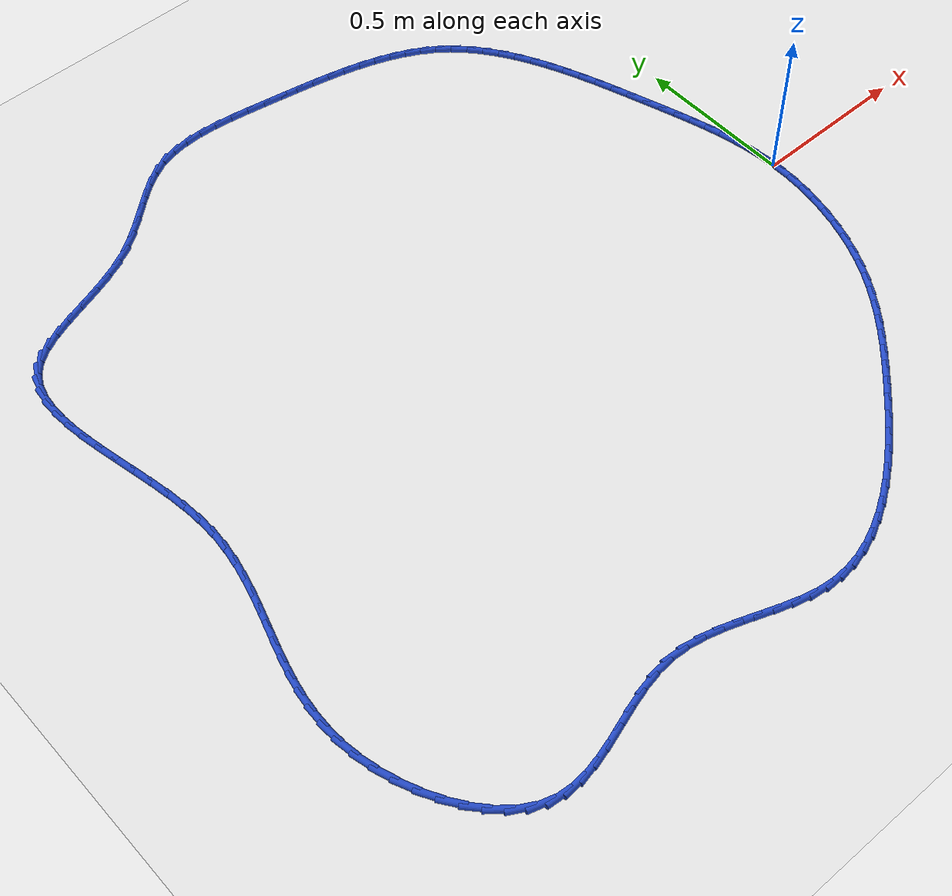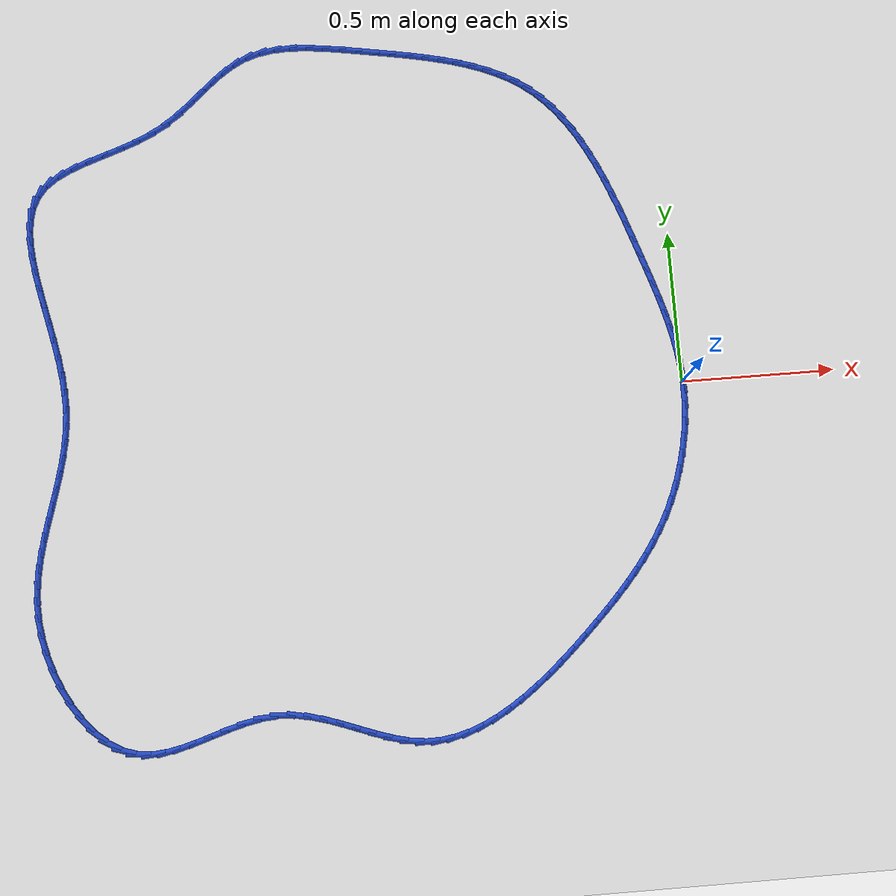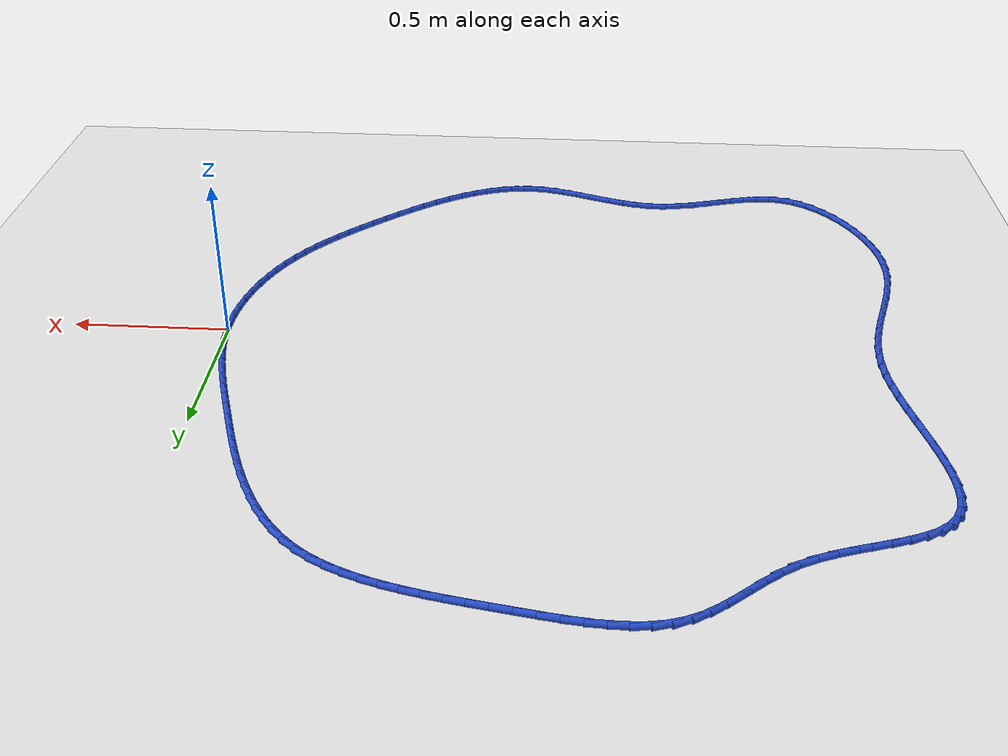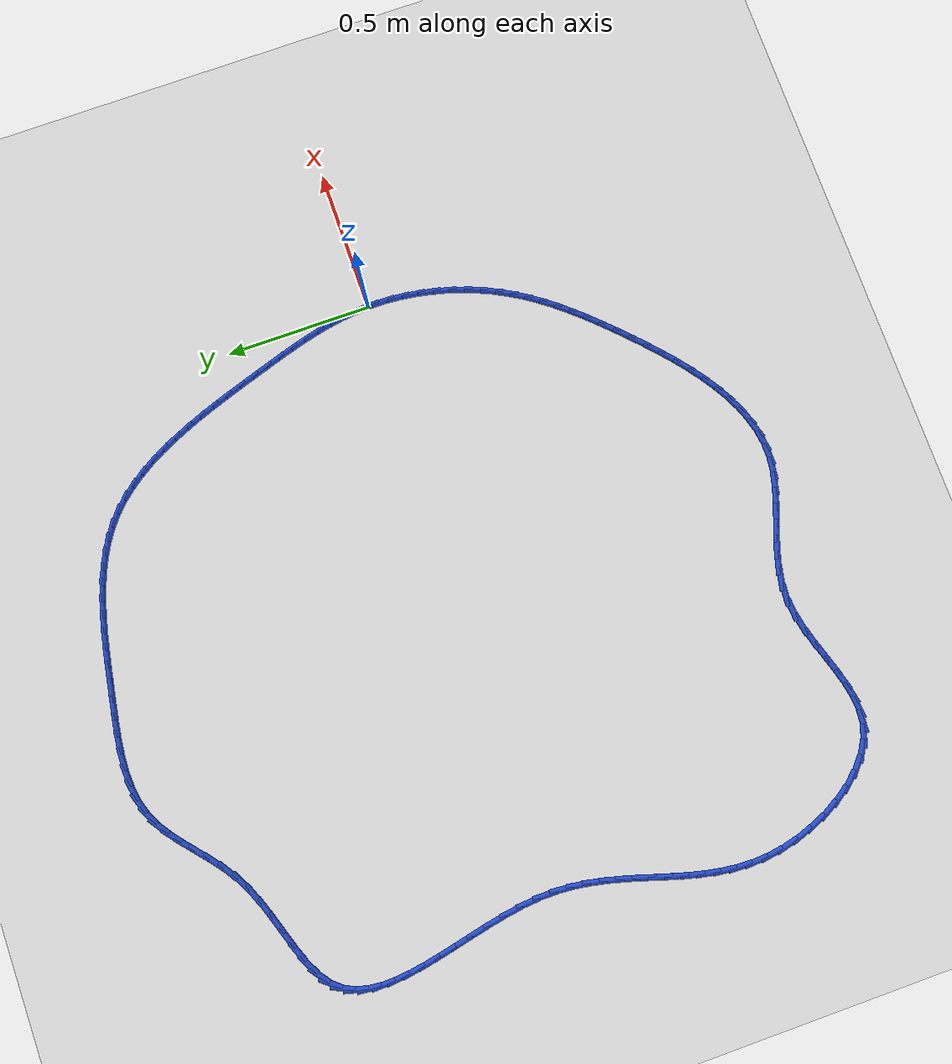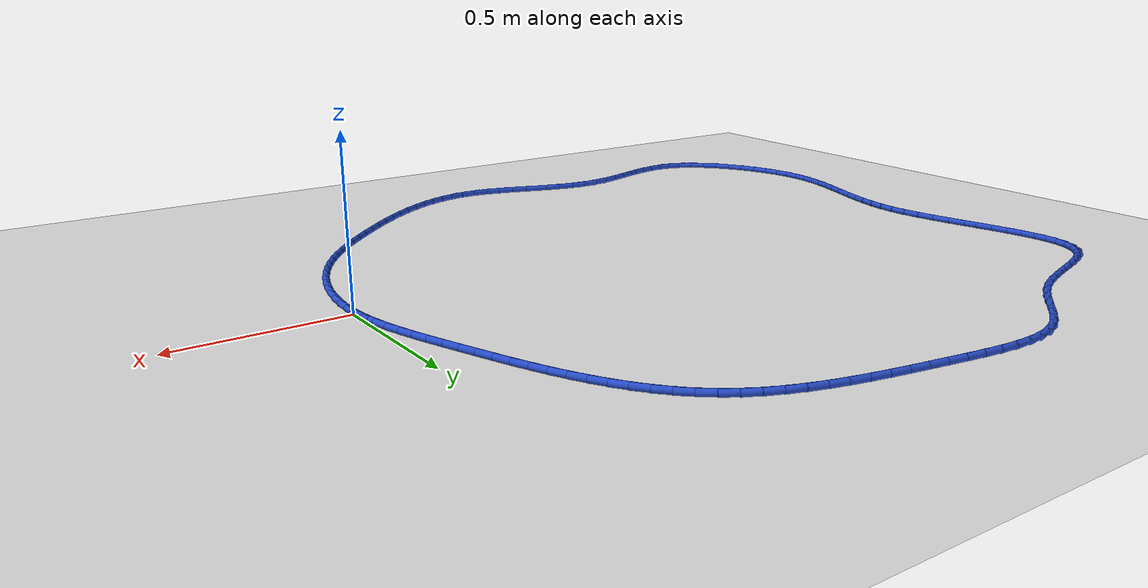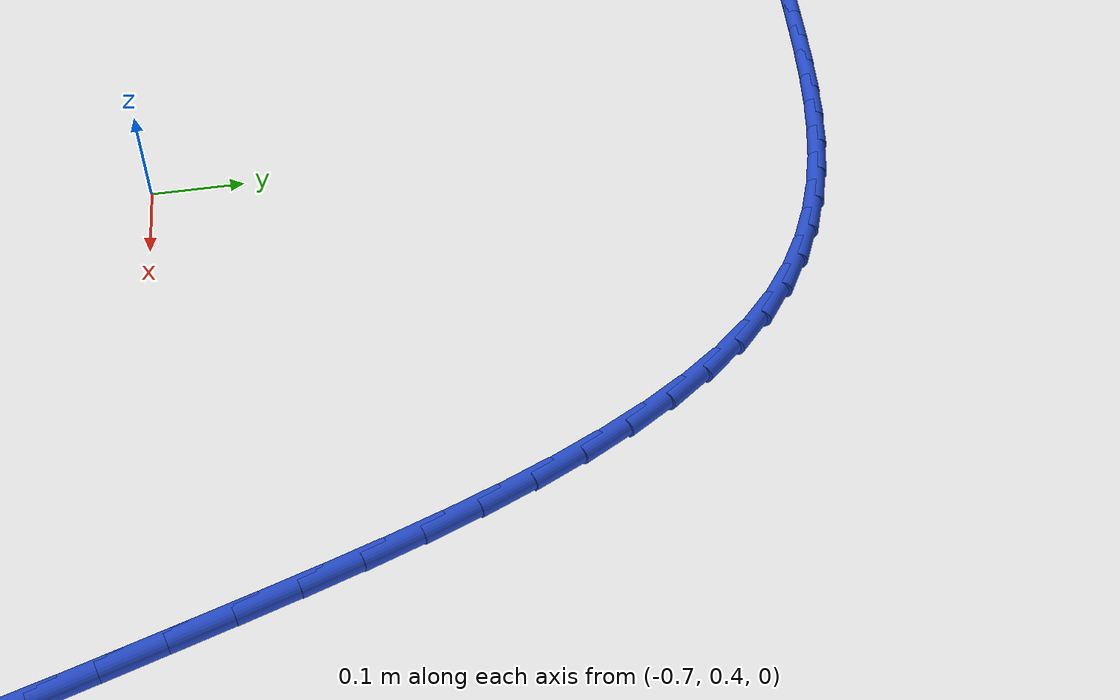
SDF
<sdf version="1.6">
 <world name="default">
  <light name="sun" type="directional">
   <pose>0 0 10 0 -0 0</pose>
   <diffuse>0.8 0.8 0.8 1</diffuse>
   <specular>0.2 0.2 0.2 1</specular>
   <attenuation>
    <range>1000</range>
    <constant>0.9</constant>
    <linear>0.01</linear>
    <quadratic>0.001</quadratic>
   </attenuation>
   <direction>-0.5 0.1 -0.9</direction>
  </light>
  <model name="ground_plane">
   <static>1</static>
   <link name="link">
    <collision name="collision">
     <geometry><plane><normal>0 0 1</normal><size>100 100</size></plane></geometry>
     <surface><friction><ode><mu>100</mu><mu2>50</mu2></ode></friction></surface>
    </collision>
    <visual name="visual">
     <cast_shadows>0</cast_shadows>
     <geometry><plane><normal>0 0 1</normal><size>100 100</size></plane></geometry>
     <material>
      <script><uri>file://media/materials/scripts/gazebo.material</uri><name>Gazebo/WhiteGlow</name></script>
     </material>
    </visual>
   </link>
  </model>
  <gravity>0 0 -9.8</gravity>
  <magnetic_field>6e-06 2.3e-05 -4.2e-05</magnetic_field>
  <atmosphere type="adiabatic"/>
  <physics name="default_physics" default="0" type="ode">
   <max_step_size>0.001</max_step_size>
   <real_time_factor>1</real_time_factor>
   <real_time_update_rate>1000</real_time_update_rate>
  </physics>
  <scene><ambient>0.4 0.4 0.4 1</ambient><background>0.7 0.7 0.7 1</background><shadows>1</shadows></scene>
  <spherical_coordinates>
   <surface_model>EARTH_WGS84</surface_model>
   <latitude_deg>0</latitude_deg>
   <longitude_deg>0</longitude_deg>
   <elevation>0</elevation>
   <heading_deg>0</heading_deg>
  </spherical_coordinates>
  <model name="line">
   <link name="link_0">
    <pose>1.734723475976807e-17 -4.163336342344337e-17 0.01 0 1.57 -1.5069342114797732</pose>
    <collision name="collision">
     <geometry><cylinder><radius>0.01</radius><length>0.08</length></cylinder></geometry>
    </collision>
    <visual name="visual">
     <material>
      <script><name>Gazebo/Blue</name><uri>file://media/materials/scripts/gazebo.material</uri></script>
     </material>
     <geometry><cylinder><radius>0.01</radius><length>0.08</length></cylinder></geometry>
    </visual>
   </link>
   <link name="link_1">
    <pose>-0.003332086898377233 0.05210531819002622 0.01 0 1.57 -1.4468177561323297</pose>
    <collision name="collision">
     <geometry><cylinder><radius>0.01</radius><length>0.08</length></cylinder></geometry>
    </collision>
    <visual name="visual">
     <material>
      <script><name>Gazebo/Blue</name><uri>file://media/materials/scripts/gazebo.material</uri></script>
     </material>
     <geometry><cylinder><radius>0.01</radius><length>0.08</length></cylinder></geometry>
    </visual>
   </link>
   <link name="link_2">
    <pose>-0.009760234622071573 0.1036882560941185 0.01 0 1.57 -1.3943022531268132</pose>
    <collision name="collision">
     <geometry><cylinder><radius>0.01</radius><length>0.08</length></cylinder></geometry>
    </collision>
    <visual name="visual">
     <material>
      <script><name>Gazebo/Blue</name><uri>file://media/materials/scripts/gazebo.material</uri></script>
     </material>
     <geometry><cylinder><radius>0.01</radius><length>0.08</length></cylinder></geometry>
    </visual>
   </link>
   <link name="link_3">
    <pose>-0.018895232684314135 0.15490781321370867 0.01 0 1.57 -1.349962863658408</pose>
    <collision name="collision">
     <geometry><cylinder><radius>0.01</radius><length>0.08</length></cylinder></geometry>
    </collision>
    <visual name="visual">
     <material>
      <script><name>Gazebo/Blue</name><uri>file://media/materials/scripts/gazebo.material</uri></script>
     </material>
     <geometry><cylinder><radius>0.01</radius><length>0.08</length></cylinder></geometry>
    </visual>
   </link>
   <link name="link_4">
    <pose>-0.030347870598336022 0.20592298905022852 0.01 0 1.57 -1.3140605316810459</pose>
    <collision name="collision">
     <geometry><cylinder><radius>0.01</radius><length>0.08</length></cylinder></geometry>
    </collision>
    <visual name="visual">
     <material>
      <script><name>Gazebo/Blue</name><uri>file://media/materials/scripts/gazebo.material</uri></script>
     </material>
     <geometry><cylinder><radius>0.01</radius><length>0.08</length></cylinder></geometry>
    </visual>
   </link>
   <link name="link_5">
    <pose>-0.04372893787736838 0.25689278310511005 0.01 0 1.57 -1.286624159305949</pose>
    <collision name="collision">
     <geometry><cylinder><radius>0.01</radius><length>0.08</length></cylinder></geometry>
    </collision>
    <visual name="visual">
     <material>
      <script><name>Gazebo/Blue</name><uri>file://media/materials/scripts/gazebo.material</uri></script>
     </material>
     <geometry><cylinder><radius>0.01</radius><length>0.08</length></cylinder></geometry>
    </visual>
   </link>
   <link name="link_6">
    <pose>-0.05864922403464233 0.30797619487978506 0.01 0 1.57 -1.2675294745256374</pose>
    <collision name="collision">
     <geometry><cylinder><radius>0.01</radius><length>0.08</length></cylinder></geometry>
    </collision>
    <visual name="visual">
     <material>
      <script><name>Gazebo/Blue</name><uri>file://media/materials/scripts/gazebo.material</uri></script>
     </material>
     <geometry><cylinder><radius>0.01</radius><length>0.08</length></cylinder></geometry>
    </visual>
   </link>
   <link name="link_7">
    <pose>-0.07471951858338899 0.35933222387568525 0.01 0 1.57 -1.2565625485777268</pose>
    <collision name="collision">
     <geometry><cylinder><radius>0.01</radius><length>0.08</length></cylinder></geometry>
    </collision>
    <visual name="visual">
     <material>
      <script><name>Gazebo/Blue</name><uri>file://media/materials/scripts/gazebo.material</uri></script>
     </material>
     <geometry><cylinder><radius>0.01</radius><length>0.08</length></cylinder></geometry>
    </visual>
   </link>
   <link name="link_8">
    <pose>-0.09155061103683948 0.4111198695942427 0.01 0 1.57 -1.2530583037774674</pose>
    <collision name="collision">
     <geometry><cylinder><radius>0.01</radius><length>0.08</length></cylinder></geometry>
    </collision>
    <visual name="visual">
     <material>
      <script><name>Gazebo/Blue</name><uri>file://media/materials/scripts/gazebo.material</uri></script>
     </material>
     <geometry><cylinder><radius>0.01</radius><length>0.08</length></cylinder></geometry>
    </visual>
   </link>
   <link name="link_9">
    <pose>-0.10877168341561973 0.4634825108003762 0.01 0 1.57 -1.249801002444167</pose>
    <collision name="collision">
     <geometry><cylinder><radius>0.01</radius><length>0.08</length></cylinder></geometry>
    </collision>
    <visual name="visual">
     <material>
      <script><name>Gazebo/Blue</name><uri>file://media/materials/scripts/gazebo.material</uri></script>
     </material>
     <geometry><cylinder><radius>0.01</radius><length>0.08</length></cylinder></geometry>
    </visual>
   </link>
   <link name="link_10">
    <pose>-0.12633078093284686 0.5162927160966634 0.01 0 1.57 -1.2408788483759607</pose>
    <collision name="collision">
     <geometry><cylinder><radius>0.01</radius><length>0.08</length></cylinder></geometry>
    </collision>
    <visual name="visual">
     <material>
      <script><name>Gazebo/Blue</name><uri>file://media/materials/scripts/gazebo.material</uri></script>
     </material>
     <geometry><cylinder><radius>0.01</radius><length>0.08</length></cylinder></geometry>
    </visual>
   </link>
   <link name="link_11">
    <pose>-0.14444584962720103 0.5691938276082817 0.01 0 1.57 -1.2260589297186144</pose>
    <collision name="collision">
     <geometry><cylinder><radius>0.01</radius><length>0.08</length></cylinder></geometry>
    </collision>
    <visual name="visual">
     <material>
      <script><name>Gazebo/Blue</name><uri>file://media/materials/scripts/gazebo.material</uri></script>
     </material>
     <geometry><cylinder><radius>0.01</radius><length>0.08</length></cylinder></geometry>
    </visual>
   </link>
   <link name="link_12">
    <pose>-0.16334335018043533 0.6218219559833138 0.01 0 1.57 -1.2051354419609097</pose>
    <collision name="collision">
     <geometry><cylinder><radius>0.01</radius><length>0.08</length></cylinder></geometry>
    </collision>
    <visual name="visual">
     <material>
      <script><name>Gazebo/Blue</name><uri>file://media/materials/scripts/gazebo.material</uri></script>
     </material>
     <geometry><cylinder><radius>0.01</radius><length>0.08</length></cylinder></geometry>
    </visual>
   </link>
   <link name="link_13">
    <pose>-0.18324974327430313 0.6738132118698424 0.01 0 1.57 -1.177749246224905</pose>
    <collision name="collision">
     <geometry><cylinder><radius>0.01</radius><length>0.08</length></cylinder></geometry>
    </collision>
    <visual name="visual">
     <material>
      <script><name>Gazebo/Blue</name><uri>file://media/materials/scripts/gazebo.material</uri></script>
     </material>
     <geometry><cylinder><radius>0.01</radius><length>0.08</length></cylinder></geometry>
    </visual>
   </link>
   <link name="link_14">
    <pose>-0.20439148959055756 0.7248037059159507 0.01 0 1.57 -1.1433948976387411</pose>
    <collision name="collision">
     <geometry><cylinder><radius>0.01</radius><length>0.08</length></cylinder></geometry>
    </collision>
    <visual name="visual">
     <material>
      <script><name>Gazebo/Blue</name><uri>file://media/materials/scripts/gazebo.material</uri></script>
     </material>
     <geometry><cylinder><radius>0.01</radius><length>0.08</length></cylinder></geometry>
    </visual>
   </link>
   <link name="link_15">
    <pose>-0.2269950498109519 0.7744295487697211 0.01 0 1.57 -1.1014331696242747</pose>
    <collision name="collision">
     <geometry><cylinder><radius>0.01</radius><length>0.08</length></cylinder></geometry>
    </collision>
    <visual name="visual">
     <material>
      <script><name>Gazebo/Blue</name><uri>file://media/materials/scripts/gazebo.material</uri></script>
     </material>
     <geometry><cylinder><radius>0.01</radius><length>0.08</length></cylinder></geometry>
    </visual>
   </link>
   <link name="link_16">
    <pose>-0.2512868846172393 0.8223268510792368 0.01 0 1.57 -1.0511178460823414</pose>
    <collision name="collision">
     <geometry><cylinder><radius>0.01</radius><length>0.08</length></cylinder></geometry>
    </collision>
    <visual name="visual">
     <material>
      <script><name>Gazebo/Blue</name><uri>file://media/materials/scripts/gazebo.material</uri></script>
     </material>
     <geometry><cylinder><radius>0.01</radius><length>0.08</length></cylinder></geometry>
    </visual>
   </link>
   <link name="link_17">
    <pose>-0.27749345469117304 0.8681317234925802 0.01 0 1.57 -0.9916496431011226</pose>
    <collision name="collision">
     <geometry><cylinder><radius>0.01</radius><length>0.08</length></cylinder></geometry>
    </collision>
    <visual name="visual">
     <material>
      <script><name>Gazebo/Blue</name><uri>file://media/materials/scripts/gazebo.material</uri></script>
     </material>
     <geometry><cylinder><radius>0.01</radius><length>0.08</length></cylinder></geometry>
    </visual>
   </link>
   <link name="link_18">
    <pose>-0.30584122071450626 0.9114802766578345 0.01 0 1.57 -0.9222741845319431</pose>
    <collision name="collision">
     <geometry><cylinder><radius>0.01</radius><length>0.08</length></cylinder></geometry>
    </collision>
    <visual name="visual">
     <material>
      <script><name>Gazebo/Blue</name><uri>file://media/materials/scripts/gazebo.material</uri></script>
     </material>
     <geometry><cylinder><radius>0.01</radius><length>0.08</length></cylinder></geometry>
    </visual>
   </link>
   <link name="link_19">
    <pose>-0.3365566433689923 0.952008621223082 0.01 0 1.57 -0.8424415244606637</pose>
    <collision name="collision">
     <geometry><cylinder><radius>0.01</radius><length>0.08</length></cylinder></geometry>
    </collision>
    <visual name="visual">
     <material>
      <script><name>Gazebo/Blue</name><uri>file://media/materials/scripts/gazebo.material</uri></script>
     </material>
     <geometry><cylinder><radius>0.01</radius><length>0.08</length></cylinder></geometry>
    </visual>
   </link>
   <link name="link_20">
    <pose>-0.3698661833363842 0.9893528678364059 0.01 0 1.57 -0.7520346070535464</pose>
    <collision name="collision">
     <geometry><cylinder><radius>0.01</radius><length>0.08</length></cylinder></geometry>
    </collision>
    <visual name="visual">
     <material>
      <script><name>Gazebo/Blue</name><uri>file://media/materials/scripts/gazebo.material</uri></script>
     </material>
     <geometry><cylinder><radius>0.01</radius><length>0.08</length></cylinder></geometry>
    </visual>
   </link>
   <link name="link_21">
    <pose>-0.40599630129843534 1.0231491271458888 0.01 0 1.57 -0.6530327148430349</pose>
    <collision name="collision">
     <geometry><cylinder><radius>0.01</radius><length>0.08</length></cylinder></geometry>
    </collision>
    <visual name="visual">
     <material>
      <script><name>Gazebo/Blue</name><uri>file://media/materials/scripts/gazebo.material</uri></script>
     </material>
     <geometry><cylinder><radius>0.01</radius><length>0.08</length></cylinder></geometry>
    </visual>
   </link>
   <link name="link_22">
    <pose>-0.4451353916823074 1.053090563587334 0.01 0 1.57 -0.5580438078330597</pose>
    <collision name="collision">
     <geometry><cylinder><radius>0.01</radius><length>0.08</length></cylinder></geometry>
    </collision>
    <visual name="visual">
     <material>
      <script><name>Gazebo/Blue</name><uri>file://media/materials/scripts/gazebo.material</uri></script>
     </material>
     <geometry><cylinder><radius>0.01</radius><length>0.08</length></cylinder></geometry>
    </visual>
   </link>
   <link name="link_23">
    <pose>-0.48716671234991993 1.0793276809645977 0.01 0 1.57 -0.473860003891663</pose>
    <collision name="collision">
     <geometry><cylinder><radius>0.01</radius><length>0.08</length></cylinder></geometry>
    </collision>
    <visual name="visual">
     <material>
      <script><name>Gazebo/Blue</name><uri>file://media/materials/scripts/gazebo.material</uri></script>
     </material>
     <geometry><cylinder><radius>0.01</radius><length>0.08</length></cylinder></geometry>
    </visual>
   </link>
   <link name="link_24">
    <pose>-0.5318268547749364 1.10223080699306 0.01 0 1.57 -0.4010669548346912</pose>
    <collision name="collision">
     <geometry><cylinder><radius>0.01</radius><length>0.08</length></cylinder></geometry>
    </collision>
    <visual name="visual">
     <material>
      <script><name>Gazebo/Blue</name><uri>file://media/materials/scripts/gazebo.material</uri></script>
     </material>
     <geometry><cylinder><radius>0.01</radius><length>0.08</length></cylinder></geometry>
    </visual>
   </link>
   <link name="link_25">
    <pose>-0.5788514777880849 1.1221716672354198 0.01 0 1.57 -0.33951286646343226</pose>
    <collision name="collision">
     <geometry><cylinder><radius>0.01</radius><length>0.08</length></cylinder></geometry>
    </collision>
    <visual name="visual">
     <material>
      <script><name>Gazebo/Blue</name><uri>file://media/materials/scripts/gazebo.material</uri></script>
     </material>
     <geometry><cylinder><radius>0.01</radius><length>0.08</length></cylinder></geometry>
    </visual>
   </link>
   <link name="link_26">
    <pose>-0.6279762402200941 1.139521987254379 0.01 0 1.57 -0.2886340486140562</pose>
    <collision name="collision">
     <geometry><cylinder><radius>0.01</radius><length>0.08</length></cylinder></geometry>
    </collision>
    <visual name="visual">
     <material>
      <script><name>Gazebo/Blue</name><uri>file://media/materials/scripts/gazebo.material</uri></script>
     </material>
     <geometry><cylinder><radius>0.01</radius><length>0.08</length></cylinder></geometry>
    </visual>
   </link>
   <link name="link_27">
    <pose>-0.678936800901692 1.1546534926126366 0.01 0 1.57 -0.24768954917802527</pose>
    <collision name="collision">
     <geometry><cylinder><radius>0.01</radius><length>0.08</length></cylinder></geometry>
    </collision>
    <visual name="visual">
     <material>
      <script><name>Gazebo/Blue</name><uri>file://media/materials/scripts/gazebo.material</uri></script>
     </material>
     <geometry><cylinder><radius>0.01</radius><length>0.08</length></cylinder></geometry>
    </visual>
   </link>
   <link name="link_28">
    <pose>-0.7314688186636075 1.1679379088728938 0.01 0 1.57 -0.21592028212821165</pose>
    <collision name="collision">
     <geometry><cylinder><radius>0.01</radius><length>0.08</length></cylinder></geometry>
    </collision>
    <visual name="visual">
     <material>
      <script><name>Gazebo/Blue</name><uri>file://media/materials/scripts/gazebo.material</uri></script>
     </material>
     <geometry><cylinder><radius>0.01</radius><length>0.08</length></cylinder></geometry>
    </visual>
   </link>
   <link name="link_29">
    <pose>-0.7853079523365687 1.1797469615978506 0.01 0 1.57 -0.19264370652524415</pose>
    <collision name="collision">
     <geometry><cylinder><radius>0.01</radius><length>0.08</length></cylinder></geometry>
    </collision>
    <visual name="visual">
     <material>
      <script><name>Gazebo/Blue</name><uri>file://media/materials/scripts/gazebo.material</uri></script>
     </material>
     <geometry><cylinder><radius>0.01</radius><length>0.08</length></cylinder></geometry>
    </visual>
   </link>
   <link name="link_30">
    <pose>-0.8401898607513043 1.1904523763502075 0.01 0 1.57 -0.17730347249409195</pose>
    <collision name="collision">
     <geometry><cylinder><radius>0.01</radius><length>0.08</length></cylinder></geometry>
    </collision>
    <visual name="visual">
     <material>
      <script><name>Gazebo/Blue</name><uri>file://media/materials/scripts/gazebo.material</uri></script>
     </material>
     <geometry><cylinder><radius>0.01</radius><length>0.08</length></cylinder></geometry>
    </visual>
   </link>
   <link name="link_31">
    <pose>-0.8958502027385422 1.2004258786926643 0.01 0 1.57 -0.16949140359172762</pose>
    <collision name="collision">
     <geometry><cylinder><radius>0.01</radius><length>0.08</length></cylinder></geometry>
    </collision>
    <visual name="visual">
     <material>
      <script><name>Gazebo/Blue</name><uri>file://media/materials/scripts/gazebo.material</uri></script>
     </material>
     <geometry><cylinder><radius>0.01</radius><length>0.08</length></cylinder></geometry>
    </visual>
   </link>
   <link name="link_32">
    <pose>-0.9520246371290115 1.2100391941879225 0.01 0 1.57 -0.16824161037010346</pose>
    <collision name="collision">
     <geometry><cylinder><radius>0.01</radius><length>0.08</length></cylinder></geometry>
    </collision>
    <visual name="visual">
     <material>
      <script><name>Gazebo/Blue</name><uri>file://media/materials/scripts/gazebo.material</uri></script>
     </material>
     <geometry><cylinder><radius>0.01</radius><length>0.08</length></cylinder></geometry>
    </visual>
   </link>
   <link name="link_33">
    <pose>-1.008443655516969 1.219621804461246 0.01 0 1.57 -0.16101649887356886</pose>
    <collision name="collision">
     <geometry><cylinder><radius>0.01</radius><length>0.08</length></cylinder></geometry>
    </collision>
    <visual name="visual">
     <material>
      <script><name>Gazebo/Blue</name><uri>file://media/materials/scripts/gazebo.material</uri></script>
     </material>
     <geometry><cylinder><radius>0.01</radius><length>0.08</length></cylinder></geometry>
    </visual>
   </link>
   <link name="link_34">
    <pose>-1.0647476810921361 1.2287668509166685 0.01 0 1.57 -0.13680526469338108</pose>
    <collision name="collision">
     <geometry><cylinder><radius>0.01</radius><length>0.08</length></cylinder></geometry>
    </collision>
    <visual name="visual">
     <material>
      <script><name>Gazebo/Blue</name><uri>file://media/materials/scripts/gazebo.material</uri></script>
     </material>
     <geometry><cylinder><radius>0.01</radius><length>0.08</length></cylinder></geometry>
    </visual>
   </link>
   <link name="link_35">
    <pose>-1.1205006407759976 1.2364420916246748 0.01 0 1.57 -0.09382537029875745</pose>
    <collision name="collision">
     <geometry><cylinder><radius>0.01</radius><length>0.08</length></cylinder></geometry>
    </collision>
    <visual name="visual">
     <material>
      <script><name>Gazebo/Blue</name><uri>file://media/materials/scripts/gazebo.material</uri></script>
     </material>
     <geometry><cylinder><radius>0.01</radius><length>0.08</length></cylinder></geometry>
    </visual>
   </link>
   <link name="link_36">
    <pose>-1.175264031399838 1.2415954178315856 0.01 0 1.57 -0.029602178520806936</pose>
    <collision name="collision">
     <geometry><cylinder><radius>0.01</radius><length>0.08</length></cylinder></geometry>
    </collision>
    <visual name="visual">
     <material>
      <script><name>Gazebo/Blue</name><uri>file://media/materials/scripts/gazebo.material</uri></script>
     </material>
     <geometry><cylinder><radius>0.01</radius><length>0.08</length></cylinder></geometry>
    </visual>
   </link>
   <link name="link_37">
    <pose>-1.2285993497949421 1.2431747207837205 0.01 0 1.57 0.05912865321763659</pose>
    <collision name="collision">
     <geometry><cylinder><radius>0.01</radius><length>0.08</length></cylinder></geometry>
    </collision>
    <visual name="visual">
     <material>
      <script><name>Gazebo/Blue</name><uri>file://media/materials/scripts/gazebo.material</uri></script>
     </material>
     <geometry><cylinder><radius>0.01</radius><length>0.08</length></cylinder></geometry>
    </visual>
   </link>
   <link name="link_38">
    <pose>-1.2800680927925936 1.240127891727399 0.01 0 1.57 0.17564114858324076</pose>
    <collision name="collision">
     <geometry><cylinder><radius>0.01</radius><length>0.08</length></cylinder></geometry>
    </collision>
    <visual name="visual">
     <material>
      <script><name>Gazebo/Blue</name><uri>file://media/materials/scripts/gazebo.material</uri></script>
     </material>
     <geometry><cylinder><radius>0.01</radius><length>0.08</length></cylinder></geometry>
    </visual>
   </link>
   <link name="link_39">
    <pose>-1.3292317572240782 1.2314028219089421 0.01 0 1.57 0.32140266014322155</pose>
    <collision name="collision">
     <geometry><cylinder><radius>0.01</radius><length>0.08</length></cylinder></geometry>
    </collision>
    <visual name="visual">
     <material>
      <script><name>Gazebo/Blue</name><uri>file://media/materials/scripts/gazebo.material</uri></script>
     </material>
     <geometry><cylinder><radius>0.01</radius><length>0.08</length></cylinder></geometry>
    </visual>
   </link>
   <link name="link_40">
    <pose>-1.3756518399206792 1.2159474025746693 0.01 0 1.57 0.4820200077810443</pose>
    <collision name="collision">
     <geometry><cylinder><radius>0.01</radius><length>0.08</length></cylinder></geometry>
    </collision>
    <visual name="visual">
     <material>
      <script><name>Gazebo/Blue</name><uri>file://media/materials/scripts/gazebo.material</uri></script>
     </material>
     <geometry><cylinder><radius>0.01</radius><length>0.08</length></cylinder></geometry>
    </visual>
   </link>
   <link name="link_41">
    <pose>-1.419141732449636 1.1931943148273474 0.01 0 1.57 0.6059103531486181</pose>
    <collision name="collision">
     <geometry><cylinder><radius>0.01</radius><length>0.08</length></cylinder></geometry>
    </collision>
    <visual name="visual">
     <material>
      <script><name>Gazebo/Blue</name><uri>file://media/materials/scripts/gazebo.material</uri></script>
     </material>
     <geometry><cylinder><radius>0.01</radius><length>0.08</length></cylinder></geometry>
    </visual>
   </link>
   <link name="link_42">
    <pose>-1.4605256017860118 1.1645215510244746 0.01 0 1.57 0.68138634217632</pose>
    <collision name="collision">
     <geometry><cylinder><radius>0.01</radius><length>0.08</length></cylinder></geometry>
    </collision>
    <visual name="visual">
     <material>
      <script><name>Gazebo/Blue</name><uri>file://media/materials/scripts/gazebo.material</uri></script>
     </material>
     <geometry><cylinder><radius>0.01</radius><length>0.08</length></cylinder></geometry>
    </visual>
   </link>
   <link name="link_43">
    <pose>-1.5008811104063229 1.1317949741703635 0.01 0 1.57 0.712633446557139</pose>
    <collision name="collision">
     <geometry><cylinder><radius>0.01</radius><length>0.08</length></cylinder></geometry>
    </collision>
    <visual name="visual">
     <material>
      <script><name>Gazebo/Blue</name><uri>file://media/materials/scripts/gazebo.material</uri></script>
     </material>
     <geometry><cylinder><radius>0.01</radius><length>0.08</length></cylinder></geometry>
    </visual>
   </link>
   <link name="link_44">
    <pose>-1.5412859207873824 1.096880447269897 0.01 0 1.57 0.7035792374951607</pose>
    <collision name="collision">
     <geometry><cylinder><radius>0.01</radius><length>0.08</length></cylinder></geometry>
    </collision>
    <visual name="visual">
     <material>
      <script><name>Gazebo/Blue</name><uri>file://media/materials/scripts/gazebo.material</uri></script>
     </material>
     <geometry><cylinder><radius>0.01</radius><length>0.08</length></cylinder></geometry>
    </visual>
   </link>
   <link name="link_45">
    <pose>-1.5828176954060023 1.0616438333279603 0.01 0 1.57 0.6564055976925861</pose>
    <collision name="collision">
     <geometry><cylinder><radius>0.01</radius><length>0.08</length></cylinder></geometry>
    </collision>
    <visual name="visual">
     <material>
      <script><name>Gazebo/Blue</name><uri>file://media/materials/scripts/gazebo.material</uri></script>
     </material>
     <geometry><cylinder><radius>0.01</radius><length>0.08</length></cylinder></geometry>
    </visual>
   </link>
   <link name="link_46">
    <pose>-1.6265540967389978 1.027950995349437 0.01 0 1.57 0.5721933192027261</pose>
    <collision name="collision">
     <geometry><cylinder><radius>0.01</radius><length>0.08</length></cylinder></geometry>
    </collision>
    <visual name="visual">
     <material>
      <script><name>Gazebo/Blue</name><uri>file://media/materials/scripts/gazebo.material</uri></script>
     </material>
     <geometry><cylinder><radius>0.01</radius><length>0.08</length></cylinder></geometry>
    </visual>
   </link>
   <link name="link_47">
    <pose>-1.6735727851841504 0.9976677938901284 0.01 0 1.57 0.4654530139055281</pose>
    <collision name="collision">
     <geometry><cylinder><radius>0.01</radius><length>0.08</length></cylinder></geometry>
    </collision>
    <visual name="visual">
     <material>
      <script><name>Gazebo/Blue</name><uri>file://media/materials/scripts/gazebo.material</uri></script>
     </material>
     <geometry><cylinder><radius>0.01</radius><length>0.08</length></cylinder></geometry>
    </visual>
   </link>
   <link name="link_48">
    <pose>-1.7244766903981563 0.9721008596638301 0.01 0 1.57 0.38432777166515913</pose>
    <collision name="collision">
     <geometry><cylinder><radius>0.01</radius><length>0.08</length></cylinder></geometry>
    </collision>
    <visual name="visual">
     <material>
      <script><name>Gazebo/Blue</name><uri>file://media/materials/scripts/gazebo.material</uri></script>
     </material>
     <geometry><cylinder><radius>0.01</radius><length>0.08</length></cylinder></geometry>
    </visual>
   </link>
   <link name="link_49">
    <pose>-1.7780622177306658 0.9504287490563782 0.01 0 1.57 0.3363972813546253</pose>
    <collision name="collision">
     <geometry><cylinder><radius>0.01</radius><length>0.08</length></cylinder></geometry>
    </collision>
    <visual name="visual">
     <material>
      <script><name>Gazebo/Blue</name><uri>file://media/materials/scripts/gazebo.material</uri></script>
     </material>
     <geometry><cylinder><radius>0.01</radius><length>0.08</length></cylinder></geometry>
    </visual>
   </link>
   <link name="link_50">
    <pose>-1.83269612759337 0.9313238994055295 0.01 0 1.57 0.31923073908143607</pose>
    <collision name="collision">
     <geometry><cylinder><radius>0.01</radius><length>0.08</length></cylinder></geometry>
    </collision>
    <visual name="visual">
     <material>
      <script><name>Gazebo/Blue</name><uri>file://media/materials/scripts/gazebo.material</uri></script>
     </material>
     <geometry><cylinder><radius>0.01</radius><length>0.08</length></cylinder></geometry>
    </visual>
   </link>
   <link name="link_51">
    <pose>-1.8867451803979576 0.913458748049041 0.01 0 1.57 0.3334429540282329</pose>
    <collision name="collision">
     <geometry><cylinder><radius>0.01</radius><length>0.08</length></cylinder></geometry>
    </collision>
    <visual name="visual">
     <material>
      <script><name>Gazebo/Blue</name><uri>file://media/materials/scripts/gazebo.material</uri></script>
     </material>
     <geometry><cylinder><radius>0.01</radius><length>0.08</length></cylinder></geometry>
    </visual>
   </link>
   <link name="link_52">
    <pose>-1.938576136556121 0.8955057323246696 0.01 0 1.57 0.3836752934981178</pose>
    <collision name="collision">
     <geometry><cylinder><radius>0.01</radius><length>0.08</length></cylinder></geometry>
    </collision>
    <visual name="visual">
     <material>
      <script><name>Gazebo/Blue</name><uri>file://media/materials/scripts/gazebo.material</uri></script>
     </material>
     <geometry><cylinder><radius>0.01</radius><length>0.08</length></cylinder></geometry>
    </visual>
   </link>
   <link name="link_53">
    <pose>-1.9865557564795493 0.8761372895701723 0.01 0 1.57 0.47977876113144247</pose>
    <collision name="collision">
     <geometry><cylinder><radius>0.01</radius><length>0.08</length></cylinder></geometry>
    </collision>
    <visual name="visual">
     <material>
      <script><name>Gazebo/Blue</name><uri>file://media/materials/scripts/gazebo.material</uri></script>
     </material>
     <geometry><cylinder><radius>0.01</radius><length>0.08</length></cylinder></geometry>
    </visual>
   </link>
   <link name="link_54">
    <pose>-2.0290508005799324 0.8540258571233063 0.01 0 1.57 0.6371221187428122</pose>
    <collision name="collision">
     <geometry><cylinder><radius>0.01</radius><length>0.08</length></cylinder></geometry>
    </collision>
    <visual name="visual">
     <material>
      <script><name>Gazebo/Blue</name><uri>file://media/materials/scripts/gazebo.material</uri></script>
     </material>
     <geometry><cylinder><radius>0.01</radius><length>0.08</length></cylinder></geometry>
    </visual>
   </link>
   <link name="link_55">
    <pose>-2.0644280292689627 0.8278438723218284 0.01 0 1.57 0.8659878204186618</pose>
    <collision name="collision">
     <geometry><cylinder><radius>0.01</radius><length>0.08</length></cylinder></geometry>
    </collision>
    <visual name="visual">
     <material>
      <script><name>Gazebo/Blue</name><uri>file://media/materials/scripts/gazebo.material</uri></script>
     </material>
     <geometry><cylinder><radius>0.01</radius><length>0.08</length></cylinder></geometry>
    </visual>
   </link>
   <link name="link_56">
    <pose>-2.0912001421006963 0.7963673314486043 0.01 0 1.57 1.1116210077133022</pose>
    <collision name="collision">
     <geometry><cylinder><radius>0.01</radius><length>0.08</length></cylinder></geometry>
    </collision>
    <visual name="visual">
     <material>
      <script><name>Gazebo/Blue</name><uri>file://media/materials/scripts/gazebo.material</uri></script>
     </material>
     <geometry><cylinder><radius>0.01</radius><length>0.08</length></cylinder></geometry>
    </visual>
   </link>
   <link name="link_57">
    <pose>-2.1094388050186703 0.7594784789947233 0.01 0 1.57 1.3194317811411482</pose>
    <collision name="collision">
     <geometry><cylinder><radius>0.01</radius><length>0.08</length></cylinder></geometry>
    </collision>
    <visual name="visual">
     <material>
      <script><name>Gazebo/Blue</name><uri>file://media/materials/scripts/gazebo.material</uri></script>
     </material>
     <geometry><cylinder><radius>0.01</radius><length>0.08</length></cylinder></geometry>
    </visual>
   </link>
   <link name="link_58">
    <pose>-2.1201597758549253 0.7177294904819285 0.01 0 1.57 1.4791441731168002</pose>
    <collision name="collision">
     <geometry><cylinder><radius>0.01</radius><length>0.08</length></cylinder></geometry>
    </collision>
    <visual name="visual">
     <material>
      <script><name>Gazebo/Blue</name><uri>file://media/materials/scripts/gazebo.material</uri></script>
     </material>
     <geometry><cylinder><radius>0.01</radius><length>0.08</length></cylinder></geometry>
    </visual>
   </link>
   <link name="link_59">
    <pose>-2.124391994150612 0.6716818952205901 0.01 0 1.57 -1.5461432372652355</pose>
    <collision name="collision">
     <geometry><cylinder><radius>0.01</radius><length>0.08</length></cylinder></geometry>
    </collision>
    <visual name="visual">
     <material>
      <script><name>Gazebo/Blue</name><uri>file://media/materials/scripts/gazebo.material</uri></script>
     </material>
     <geometry><cylinder><radius>0.01</radius><length>0.08</length></cylinder></geometry>
    </visual>
   </link>
   <link name="link_60">
    <pose>-2.123164399446884 0.6218972225210803 0.01 0 1.57 -1.4643563840563643</pose>
    <collision name="collision">
     <geometry><cylinder><radius>0.01</radius><length>0.08</length></cylinder></geometry>
    </collision>
    <visual name="visual">
     <material>
      <script><name>Gazebo/Blue</name><uri>file://media/materials/scripts/gazebo.material</uri></script>
     </material>
     <geometry><cylinder><radius>0.01</radius><length>0.08</length></cylinder></geometry>
    </visual>
   </link>
   <link name="link_61">
    <pose>-2.1175059312848923 0.568937001693769 0.01 0 1.57 -1.409185755806936</pose>
    <collision name="collision">
     <geometry><cylinder><radius>0.01</radius><length>0.08</length></cylinder></geometry>
    </collision>
    <visual name="visual">
     <material>
      <script><name>Gazebo/Blue</name><uri>file://media/materials/scripts/gazebo.material</uri></script>
     </material>
     <geometry><cylinder><radius>0.01</radius><length>0.08</length></cylinder></geometry>
    </visual>
   </link>
   <link name="link_62">
    <pose>-2.1084455292057895 0.5133627620490288 0.01 0 1.57 -1.374935470202558</pose>
    <collision name="collision">
     <geometry><cylinder><radius>0.01</radius><length>0.08</length></cylinder></geometry>
    </collision>
    <visual name="visual">
     <material>
      <script><name>Gazebo/Blue</name><uri>file://media/materials/scripts/gazebo.material</uri></script>
     </material>
     <geometry><cylinder><radius>0.01</radius><length>0.08</length></cylinder></geometry>
    </visual>
   </link>
   <link name="link_63">
    <pose>-2.097012132750727 0.45573603289722925 0.01 0 1.57 -1.3579347675063826</pose>
    <collision name="collision">
     <geometry><cylinder><radius>0.01</radius><length>0.08</length></cylinder></geometry>
    </collision>
    <visual name="visual">
     <material>
      <script><name>Gazebo/Blue</name><uri>file://media/materials/scripts/gazebo.material</uri></script>
     </material>
     <geometry><cylinder><radius>0.01</radius><length>0.08</length></cylinder></geometry>
    </visual>
   </link>
   <link name="link_64">
    <pose>-2.084234681460858 0.39661834354874276 0.01 0 1.57 -1.3561180135367037</pose>
    <collision name="collision">
     <geometry><cylinder><radius>0.01</radius><length>0.08</length></cylinder></geometry>
    </collision>
    <visual name="visual">
     <material>
      <script><name>Gazebo/Blue</name><uri>file://media/materials/scripts/gazebo.material</uri></script>
     </material>
     <geometry><cylinder><radius>0.01</radius><length>0.08</length></cylinder></geometry>
    </visual>
   </link>
   <link name="link_65">
    <pose>-2.071142114877335 0.33657122331394007 0.01 0 1.57 -1.3686983949951808</pose>
    <collision name="collision">
     <geometry><cylinder><radius>0.01</radius><length>0.08</length></cylinder></geometry>
    </collision>
    <visual name="visual">
     <material>
      <script><name>Gazebo/Blue</name><uri>file://media/materials/scripts/gazebo.material</uri></script>
     </material>
     <geometry><cylinder><radius>0.01</radius><length>0.08</length></cylinder></geometry>
    </visual>
   </link>
   <link name="link_66">
    <pose>-2.0587633725413075 0.2761562015031914 0.01 0 1.57 -1.3959844507596084</pose>
    <collision name="collision">
     <geometry><cylinder><radius>0.01</radius><length>0.08</length></cylinder></geometry>
    </collision>
    <visual name="visual">
     <material>
      <script><name>Gazebo/Blue</name><uri>file://media/materials/scripts/gazebo.material</uri></script>
     </material>
     <geometry><cylinder><radius>0.01</radius><length>0.08</length></cylinder></geometry>
    </visual>
   </link>
   <link name="link_67">
    <pose>-2.048127393993929 0.21593480742686932 0.01 0 1.57 -1.4393115807158987</pose>
    <collision name="collision">
     <geometry><cylinder><radius>0.01</radius><length>0.08</length></cylinder></geometry>
    </collision>
    <visual name="visual">
     <material>
      <script><name>Gazebo/Blue</name><uri>file://media/materials/scripts/gazebo.material</uri></script>
     </material>
     <geometry><cylinder><radius>0.01</radius><length>0.08</length></cylinder></geometry>
    </visual>
   </link>
   <link name="link_68">
    <pose>-2.0402631187763522 0.15646857039534362 0.01 0 1.57 -1.5010273152706755</pose>
    <collision name="collision">
     <geometry><cylinder><radius>0.01</radius><length>0.08</length></cylinder></geometry>
    </collision>
    <visual name="visual">
     <material>
      <script><name>Gazebo/Blue</name><uri>file://media/materials/scripts/gazebo.material</uri></script>
     </material>
     <geometry><cylinder><radius>0.01</radius><length>0.08</length></cylinder></geometry>
    </visual>
   </link>
   <link name="link_69">
    <pose>-2.036199486429729 0.09831901971898656 0.01 0 1.57 1.5599807815392224</pose>
    <collision name="collision">
     <geometry><cylinder><radius>0.01</radius><length>0.08</length></cylinder></geometry>
    </collision>
    <visual name="visual">
     <material>
      <script><name>Gazebo/Blue</name><uri>file://media/materials/scripts/gazebo.material</uri></script>
     </material>
     <geometry><cylinder><radius>0.01</radius><length>0.08</length></cylinder></geometry>
    </visual>
   </link>
   <link name="link_70">
    <pose>-2.036808897063593 0.04197540900590196 0.01 0 1.57 1.4793092069854739</pose>
    <collision name="collision">
     <geometry><cylinder><radius>0.01</radius><length>0.08</length></cylinder></geometry>
    </collision>
    <visual name="visual">
     <material>
      <script><name>Gazebo/Blue</name><uri>file://media/materials/scripts/gazebo.material</uri></script>
     </material>
     <geometry><cylinder><radius>0.01</radius><length>0.08</length></cylinder></geometry>
    </visual>
   </link>
   <link name="link_71">
    <pose>-2.041816086609694 -0.012602895293041863 0.01 0 1.57 1.4098534217162904</pose>
    <collision name="collision">
     <geometry><cylinder><radius>0.01</radius><length>0.08</length></cylinder></geometry>
    </collision>
    <visual name="visual">
     <material>
      <script><name>Gazebo/Blue</name><uri>file://media/materials/scripts/gazebo.material</uri></script>
     </material>
     <geometry><cylinder><radius>0.01</radius><length>0.08</length></cylinder></geometry>
    </visual>
   </link>
   <link name="link_72">
    <pose>-2.050435005796596 -0.06569236097580525 0.01 0 1.57 1.3537116298803245</pose>
    <collision name="collision">
     <geometry><cylinder><radius>0.01</radius><length>0.08</length></cylinder></geometry>
    </collision>
    <visual name="visual">
     <material>
      <script><name>Gazebo/Blue</name><uri>file://media/materials/scripts/gazebo.material</uri></script>
     </material>
     <geometry><cylinder><radius>0.01</radius><length>0.08</length></cylinder></geometry>
    </visual>
   </link>
   <link name="link_73">
    <pose>-2.061877272166428 -0.11757053309408935 0.01 0 1.57 1.3121732466424174</pose>
    <collision name="collision">
     <geometry><cylinder><radius>0.01</radius><length>0.08</length></cylinder></geometry>
    </collision>
    <visual name="visual">
     <material>
      <script><name>Gazebo/Blue</name><uri>file://media/materials/scripts/gazebo.material</uri></script>
     </material>
     <geometry><cylinder><radius>0.01</radius><length>0.08</length></cylinder></geometry>
    </visual>
   </link>
   <link name="link_74">
    <pose>-2.075354503261318 -0.1685149566995929 0.01 0 1.57 1.2859686330386246</pose>
    <collision name="collision">
     <geometry><cylinder><radius>0.01</radius><length>0.08</length></cylinder></geometry>
    </collision>
    <visual name="visual">
     <material>
      <script><name>Gazebo/Blue</name><uri>file://media/materials/scripts/gazebo.material</uri></script>
     </material>
     <geometry><cylinder><radius>0.01</radius><length>0.08</length></cylinder></geometry>
    </visual>
   </link>
   <link name="link_75">
    <pose>-2.090078316623393 -0.21880317684401698 0.01 0 1.57 1.2754995097951047</pose>
    <collision name="collision">
     <geometry><cylinder><radius>0.01</radius><length>0.08</length></cylinder></geometry>
    </collision>
    <visual name="visual">
     <material>
      <script><name>Gazebo/Blue</name><uri>file://media/materials/scripts/gazebo.material</uri></script>
     </material>
     <geometry><cylinder><radius>0.01</radius><length>0.08</length></cylinder></geometry>
    </visual>
   </link>
   <link name="link_76">
    <pose>-2.105260329794781 -0.268712738579062 0.01 0 1.57 1.281011062429523</pose>
    <collision name="collision">
     <geometry><cylinder><radius>0.01</radius><length>0.08</length></cylinder></geometry>
    </collision>
    <visual name="visual">
     <material>
      <script><name>Gazebo/Blue</name><uri>file://media/materials/scripts/gazebo.material</uri></script>
     </material>
     <geometry><cylinder><radius>0.01</radius><length>0.08</length></cylinder></geometry>
    </visual>
   </link>
   <link name="link_77">
    <pose>-2.1201121603176123 -0.31852118695642834 0.01 0 1.57 1.3026640490277204</pose>
    <collision name="collision">
     <geometry><cylinder><radius>0.01</radius><length>0.08</length></cylinder></geometry>
    </collision>
    <visual name="visual">
     <material>
      <script><name>Gazebo/Blue</name><uri>file://media/materials/scripts/gazebo.material</uri></script>
     </material>
     <geometry><cylinder><radius>0.01</radius><length>0.08</length></cylinder></geometry>
    </visual>
   </link>
   <link name="link_78">
    <pose>-2.1338454257340125 -0.36850606702781685 0.01 0 1.57 1.3404882086399208</pose>
    <collision name="collision">
     <geometry><cylinder><radius>0.01</radius><length>0.08</length></cylinder></geometry>
    </collision>
    <visual name="visual">
     <material>
      <script><name>Gazebo/Blue</name><uri>file://media/materials/scripts/gazebo.material</uri></script>
     </material>
     <geometry><cylinder><radius>0.01</radius><length>0.08</length></cylinder></geometry>
    </visual>
   </link>
   <link name="link_79">
    <pose>-2.145671743586111 -0.41894492384492665 0.01 0 1.57 1.3942120856133386</pose>
    <collision name="collision">
     <geometry><cylinder><radius>0.01</radius><length>0.08</length></cylinder></geometry>
    </collision>
    <visual name="visual">
     <material>
      <script><name>Gazebo/Blue</name><uri>file://media/materials/scripts/gazebo.material</uri></script>
     </material>
     <geometry><cylinder><radius>0.01</radius><length>0.08</length></cylinder></geometry>
    </visual>
   </link>
   <link name="link_80">
    <pose>-2.154802731416035 -0.47011530245945854 0.01 0 1.57 1.4629879823273253</pose>
    <collision name="collision">
     <geometry><cylinder><radius>0.01</radius><length>0.08</length></cylinder></geometry>
    </collision>
    <visual name="visual">
     <material>
      <script><name>Gazebo/Blue</name><uri>file://media/materials/scripts/gazebo.material</uri></script>
     </material>
     <geometry><cylinder><radius>0.01</radius><length>0.08</length></cylinder></geometry>
    </visual>
   </link>
   <link name="link_81">
    <pose>-2.160450006765913 -0.522294747923113 0.01 0 1.57 1.545081371370984</pose>
    <collision name="collision">
     <geometry><cylinder><radius>0.01</radius><length>0.08</length></cylinder></geometry>
    </collision>
    <visual name="visual">
     <material>
      <script><name>Gazebo/Blue</name><uri>file://media/materials/scripts/gazebo.material</uri></script>
     </material>
     <geometry><cylinder><radius>0.01</radius><length>0.08</length></cylinder></geometry>
    </visual>
   </link>
   <link name="link_82">
    <pose>-2.1618251871778735 -0.5757608052875912 0.01 0 1.57 -1.5039275746834406</pose>
    <collision name="collision">
     <geometry><cylinder><radius>0.01</radius><length>0.08</length></cylinder></geometry>
    </collision>
    <visual name="visual">
     <material>
      <script><name>Gazebo/Blue</name><uri>file://media/materials/scripts/gazebo.material</uri></script>
     </material>
     <geometry><cylinder><radius>0.01</radius><length>0.08</length></cylinder></geometry>
    </visual>
   </link>
   <link name="link_83">
    <pose>-2.1581398910065146 -0.6307910184904844 0.01 0 1.57 -1.4073664089988973</pose>
    <collision name="collision">
     <geometry><cylinder><radius>0.01</radius><length>0.08</length></cylinder></geometry>
    </collision>
    <visual name="visual">
     <material>
      <script><name>Gazebo/Blue</name><uri>file://media/materials/scripts/gazebo.material</uri></script>
     </material>
     <geometry><cylinder><radius>0.01</radius><length>0.08</length></cylinder></geometry>
    </visual>
   </link>
   <link name="link_84">
    <pose>-2.1488072384815595 -0.687386620226159 0.01 0 1.57 -1.3172382843445793</pose>
    <collision name="collision">
     <geometry><cylinder><radius>0.01</radius><length>0.08</length></cylinder></geometry>
    </collision>
    <visual name="visual">
     <material>
      <script><name>Gazebo/Blue</name><uri>file://media/materials/scripts/gazebo.material</uri></script>
     </material>
     <geometry><cylinder><radius>0.01</radius><length>0.08</length></cylinder></geometry>
    </visual>
   </link>
   <link name="link_85">
    <pose>-2.1340081942255127 -0.7444959297178624 0.01 0 1.57 -1.2311287377189504</pose>
    <collision name="collision">
     <geometry><cylinder><radius>0.01</radius><length>0.08</length></cylinder></geometry>
    </collision>
    <visual name="visual">
     <material>
      <script><name>Gazebo/Blue</name><uri>file://media/materials/scripts/gazebo.material</uri></script>
     </material>
     <geometry><cylinder><radius>0.01</radius><length>0.08</length></cylinder></geometry>
    </visual>
   </link>
   <link name="link_86">
    <pose>-2.1141065908210224 -0.8008165068677064 0.01 0 1.57 -1.1443124911233582</pose>
    <collision name="collision">
     <geometry><cylinder><radius>0.01</radius><length>0.08</length></cylinder></geometry>
    </collision>
    <visual name="visual">
     <material>
      <script><name>Gazebo/Blue</name><uri>file://media/materials/scripts/gazebo.material</uri></script>
     </material>
     <geometry><cylinder><radius>0.01</radius><length>0.08</length></cylinder></geometry>
    </visual>
   </link>
   <link name="link_87">
    <pose>-2.0894662608507377 -0.8550459115778044 0.01 0 1.57 -1.0521515799140335</pose>
    <collision name="collision">
     <geometry><cylinder><radius>0.01</radius><length>0.08</length></cylinder></geometry>
    </collision>
    <visual name="visual">
     <material>
      <script><name>Gazebo/Blue</name><uri>file://media/materials/scripts/gazebo.material</uri></script>
     </material>
     <geometry><cylinder><radius>0.01</radius><length>0.08</length></cylinder></geometry>
    </visual>
   </link>
   <link name="link_88">
    <pose>-2.060451036897307 -0.9058817037502667 0.01 0 1.57 -0.9495525976556473</pose>
    <collision name="collision">
     <geometry><cylinder><radius>0.01</radius><length>0.08</length></cylinder></geometry>
    </collision>
    <visual name="visual">
     <material>
      <script><name>Gazebo/Blue</name><uri>file://media/materials/scripts/gazebo.material</uri></script>
     </material>
     <geometry><cylinder><radius>0.01</radius><length>0.08</length></cylinder></geometry>
    </visual>
   </link>
   <link name="link_89">
    <pose>-2.0274247515433785 -0.9520214432872057 0.01 0 1.57 -0.8305116250608461</pose>
    <collision name="collision">
     <geometry><cylinder><radius>0.01</radius><length>0.08</length></cylinder></geometry>
    </collision>
    <visual name="visual">
     <material>
      <script><name>Gazebo/Blue</name><uri>file://media/materials/scripts/gazebo.material</uri></script>
     </material>
     <geometry><cylinder><radius>0.01</radius><length>0.08</length></cylinder></geometry>
    </visual>
   </link>
   <link name="link_90">
    <pose>-1.9907512373715994 -0.992162690090734 0.01 0 1.57 -0.6879486404382746</pose>
    <collision name="collision">
     <geometry><cylinder><radius>0.01</radius><length>0.08</length></cylinder></geometry>
    </collision>
    <visual name="visual">
     <material>
      <script><name>Gazebo/Blue</name><uri>file://media/materials/scripts/gazebo.material</uri></script>
     </material>
     <geometry><cylinder><radius>0.01</radius><length>0.08</length></cylinder></geometry>
    </visual>
   </link>
   <link name="link_91">
    <pose>-1.9507943269646197 -1.0250030040629643 0.01 0 1.57 -0.5144939502764552</pose>
    <collision name="collision">
     <geometry><cylinder><radius>0.01</radius><length>0.08</length></cylinder></geometry>
    </collision>
    <visual name="visual">
     <material>
      <script><name>Gazebo/Blue</name><uri>file://media/materials/scripts/gazebo.material</uri></script>
     </material>
     <geometry><cylinder><radius>0.01</radius><length>0.08</length></cylinder></geometry>
    </visual>
   </link>
   <link name="link_92">
    <pose>-1.9079178529050864 -1.0492399451060066 0.01 0 1.57 -0.3056353205813546</pose>
    <collision name="collision">
     <geometry><cylinder><radius>0.01</radius><length>0.08</length></cylinder></geometry>
    </collision>
    <visual name="visual">
     <material>
      <script><name>Gazebo/Blue</name><uri>file://media/materials/scripts/gazebo.material</uri></script>
     </material>
     <geometry><cylinder><radius>0.01</radius><length>0.08</length></cylinder></geometry>
    </visual>
   </link>
   <link name="link_93">
    <pose>-1.8624856074091414 -1.063574802433269 0.01 0 1.57 -0.08546857987774055</pose>
    <collision name="collision">
     <geometry><cylinder><radius>0.01</radius><length>0.08</length></cylinder></geometry>
    </collision>
    <visual name="visual">
     <material>
      <script><name>Gazebo/Blue</name><uri>file://media/materials/scripts/gazebo.material</uri></script>
     </material>
     <geometry><cylinder><radius>0.01</radius><length>0.08</length></cylinder></geometry>
    </visual>
   </link>
   <link name="link_94">
    <pose>-1.8148511308385575 -1.0676559958821255 0.01 0 1.57 0.08720620300349631</pose>
    <collision name="collision">
     <geometry><cylinder><radius>0.01</radius><length>0.08</length></cylinder></geometry>
    </collision>
    <visual name="visual">
     <material>
      <script><name>Gazebo/Blue</name><uri>file://media/materials/scripts/gazebo.material</uri></script>
     </material>
     <geometry><cylinder><radius>0.01</radius><length>0.08</length></cylinder></geometry>
    </visual>
   </link>
   <link name="link_95">
    <pose>-1.7653441963756578 -1.0633277064374638 0.01 0 1.57 0.20440431136502302</pose>
    <collision name="collision">
     <geometry><cylinder><radius>0.01</radius><length>0.08</length></cylinder></geometry>
    </collision>
    <visual name="visual">
     <material>
      <script><name>Gazebo/Blue</name><uri>file://media/materials/scripts/gazebo.material</uri></script>
     </material>
     <geometry><cylinder><radius>0.01</radius><length>0.08</length></cylinder></geometry>
    </visual>
   </link>
   <link name="link_96">
    <pose>-1.7142912180795937 -1.0527444519570812 0.01 0 1.57 0.27384885898415534</pose>
    <collision name="collision">
     <geometry><cylinder><radius>0.01</radius><length>0.08</length></cylinder></geometry>
    </collision>
    <visual name="visual">
     <material>
      <script><name>Gazebo/Blue</name><uri>file://media/materials/scripts/gazebo.material</uri></script>
     </material>
     <geometry><cylinder><radius>0.01</radius><length>0.08</length></cylinder></geometry>
    </visual>
   </link>
   <link name="link_97">
    <pose>-1.662018610009516 -1.0380607502987762 0.01 0 1.57 0.3031472118898818</pose>
    <collision name="collision">
     <geometry><cylinder><radius>0.01</radius><length>0.08</length></cylinder></geometry>
    </collision>
    <visual name="visual">
     <material>
      <script><name>Gazebo/Blue</name><uri>file://media/materials/scripts/gazebo.material</uri></script>
     </material>
     <geometry><cylinder><radius>0.01</radius><length>0.08</length></cylinder></geometry>
    </visual>
   </link>
   <link name="link_98">
    <pose>-1.6088527862245754 -1.0214311193203454 0.01 0 1.57 0.2965924510276212</pose>
    <collision name="collision">
     <geometry><cylinder><radius>0.01</radius><length>0.08</length></cylinder></geometry>
    </collision>
    <visual name="visual">
     <material>
      <script><name>Gazebo/Blue</name><uri>file://media/materials/scripts/gazebo.material</uri></script>
     </material>
     <geometry><cylinder><radius>0.01</radius><length>0.08</length></cylinder></geometry>
    </visual>
   </link>
   <link name="link_99">
    <pose>-1.5551201607839236 -1.0050100768795873 0.01 0 1.57 0.2548010532948569</pose>
    <collision name="collision">
     <geometry><cylinder><radius>0.01</radius><length>0.08</length></cylinder></geometry>
    </collision>
    <visual name="visual">
     <material>
      <script><name>Gazebo/Blue</name><uri>file://media/materials/scripts/gazebo.material</uri></script>
     </material>
     <geometry><cylinder><radius>0.01</radius><length>0.08</length></cylinder></geometry>
    </visual>
   </link>
   <link name="link_100">
    <pose>-1.5011471477467095 -0.9909521408342992 0.01 0 1.57 0.1752272332510406</pose>
    <collision name="collision">
     <geometry><cylinder><radius>0.01</radius><length>0.08</length></cylinder></geometry>
    </collision>
    <visual name="visual">
     <material>
      <script><name>Gazebo/Blue</name><uri>file://media/materials/scripts/gazebo.material</uri></script>
     </material>
     <geometry><cylinder><radius>0.01</radius><length>0.08</length></cylinder></geometry>
    </visual>
   </link>
   <link name="link_101">
    <pose>-1.4472601611720872 -0.9814118290422792 0.01 0 1.57 0.05374125069389316</pose>
    <collision name="collision">
     <geometry><cylinder><radius>0.01</radius><length>0.08</length></cylinder></geometry>
    </collision>
    <visual name="visual">
     <material>
      <script><name>Gazebo/Blue</name><uri>file://media/materials/scripts/gazebo.material</uri></script>
     </material>
     <geometry><cylinder><radius>0.01</radius><length>0.08</length></cylinder></geometry>
    </visual>
   </link>
   <link name="link_102">
    <pose>-1.3937847885720749 -0.9785352257769919 0.01 0 1.57 -0.0895634365511266</pose>
    <collision name="collision">
     <geometry><cylinder><radius>0.01</radius><length>0.08</length></cylinder></geometry>
    </collision>
    <visual name="visual">
     <material>
      <script><name>Gazebo/Blue</name><uri>file://media/materials/scripts/gazebo.material</uri></script>
     </material>
     <geometry><cylinder><radius>0.01</radius><length>0.08</length></cylinder></geometry>
    </visual>
   </link>
   <link name="link_103">
    <pose>-1.3409303166233932 -0.9832817523077103 0.01 0 1.57 -0.2061603961926611</pose>
    <collision name="collision">
     <geometry><cylinder><radius>0.01</radius><length>0.08</length></cylinder></geometry>
    </collision>
    <visual name="visual">
     <material>
      <script><name>Gazebo/Blue</name><uri>file://media/materials/scripts/gazebo.material</uri></script>
     </material>
     <geometry><cylinder><radius>0.01</radius><length>0.08</length></cylinder></geometry>
    </visual>
   </link>
   <link name="link_104">
    <pose>-1.2886708198576018 -0.9942108682001728 0.01 0 1.57 -0.28907804782855057</pose>
    <collision name="collision">
     <geometry><cylinder><radius>0.01</radius><length>0.08</length></cylinder></geometry>
    </collision>
    <visual name="visual">
     <material>
      <script><name>Gazebo/Blue</name><uri>file://media/materials/scripts/gazebo.material</uri></script>
     </material>
     <geometry><cylinder><radius>0.01</radius><length>0.08</length></cylinder></geometry>
    </visual>
   </link>
   <link name="link_105">
    <pose>-1.2369519978161658 -1.009592511875211 0.01 0 1.57 -0.3396756180776072</pose>
    <collision name="collision">
     <geometry><cylinder><radius>0.01</radius><length>0.08</length></cylinder></geometry>
    </collision>
    <visual name="visual">
     <material>
      <script><name>Gazebo/Blue</name><uri>file://media/materials/scripts/gazebo.material</uri></script>
     </material>
     <geometry><cylinder><radius>0.01</radius><length>0.08</length></cylinder></geometry>
    </visual>
   </link>
   <link name="link_106">
    <pose>-1.1857195500405482 -1.0276966217536565 0.01 0 1.57 -0.35957075655431037</pose>
    <collision name="collision">
     <geometry><cylinder><radius>0.01</radius><length>0.08</length></cylinder></geometry>
    </collision>
    <visual name="visual">
     <material>
      <script><name>Gazebo/Blue</name><uri>file://media/materials/scripts/gazebo.material</uri></script>
     </material>
     <geometry><cylinder><radius>0.01</radius><length>0.08</length></cylinder></geometry>
    </visual>
   </link>
   <link name="link_107">
    <pose>-1.1349191760722148 -1.046793136256343 0.01 0 1.57 -0.3491802331097469</pose>
    <collision name="collision">
     <geometry><cylinder><radius>0.01</radius><length>0.08</length></cylinder></geometry>
    </collision>
    <visual name="visual">
     <material>
      <script><name>Gazebo/Blue</name><uri>file://media/materials/scripts/gazebo.material</uri></script>
     </material>
     <geometry><cylinder><radius>0.01</radius><length>0.08</length></cylinder></geometry>
    </visual>
   </link>
   <link name="link_108">
    <pose>-1.0844965754526297 -1.0651519938041012 0.01 0 1.57 -0.3071554523126123</pose>
    <collision name="collision">
     <geometry><cylinder><radius>0.01</radius><length>0.08</length></cylinder></geometry>
    </collision>
    <visual name="visual">
     <material>
      <script><name>Gazebo/Blue</name><uri>file://media/materials/scripts/gazebo.material</uri></script>
     </material>
     <geometry><cylinder><radius>0.01</radius><length>0.08</length></cylinder></geometry>
    </visual>
   </link>
   <link name="link_109">
    <pose>-1.0343974477232567 -1.0810431328177643 0.01 0 1.57 -0.23049470551610435</pose>
    <collision name="collision">
     <geometry><cylinder><radius>0.01</radius><length>0.08</length></cylinder></geometry>
    </collision>
    <visual name="visual">
     <material>
      <script><name>Gazebo/Blue</name><uri>file://media/materials/scripts/gazebo.material</uri></script>
     </material>
     <geometry><cylinder><radius>0.01</radius><length>0.08</length></cylinder></geometry>
    </visual>
   </link>
   <link name="link_110">
    <pose>-0.9845674924255619 -1.0927364917181634 0.01 0 1.57 -0.11574833551960549</pose>
    <collision name="collision">
     <geometry><cylinder><radius>0.01</radius><length>0.08</length></cylinder></geometry>
    </collision>
    <visual name="visual">
     <material>
      <script><name>Gazebo/Blue</name><uri>file://media/materials/scripts/gazebo.material</uri></script>
     </material>
     <geometry><cylinder><radius>0.01</radius><length>0.08</length></cylinder></geometry>
    </visual>
   </link>
   <link name="link_111">
    <pose>-0.9349526061661336 -1.0985051173203935 0.01 0 1.57 0.0246745908671245</pose>
    <collision name="collision">
     <geometry><cylinder><radius>0.01</radius><length>0.08</length></cylinder></geometry>
    </collision>
    <visual name="visual">
     <material>
      <script><name>Gazebo/Blue</name><uri>file://media/materials/scripts/gazebo.material</uri></script>
     </material>
     <geometry><cylinder><radius>0.01</radius><length>0.08</length></cylinder></geometry>
    </visual>
   </link>
   <link name="link_112">
    <pose>-0.8855407560410551 -1.0972856526400876 0.01 0 1.57 0.15722142728989127</pose>
    <collision name="collision">
     <geometry><cylinder><radius>0.01</radius><length>0.08</length></cylinder></geometry>
    </collision>
    <visual name="visual">
     <material>
      <script><name>Gazebo/Blue</name><uri>file://media/materials/scripts/gazebo.material</uri></script>
     </material>
     <geometry><cylinder><radius>0.01</radius><length>0.08</length></cylinder></geometry>
    </visual>
   </link>
   <link name="link_113">
    <pose>-0.8364139181074226 -1.0894975850832735 0.01 0 1.57 0.2746629365647314</pose>
    <collision name="collision">
     <geometry><cylinder><radius>0.01</radius><length>0.08</length></cylinder></geometry>
    </collision>
    <visual name="visual">
     <material>
      <script><name>Gazebo/Blue</name><uri>file://media/materials/scripts/gazebo.material</uri></script>
     </material>
     <geometry><cylinder><radius>0.01</radius><length>0.08</length></cylinder></geometry>
    </visual>
   </link>
   <link name="link_114">
    <pose>-0.7876668108203452 -1.0757613934636507 0.01 0 1.57 0.37611938677544743</pose>
    <collision name="collision">
     <geometry><cylinder><radius>0.01</radius><length>0.08</length></cylinder></geometry>
    </collision>
    <visual name="visual">
     <material>
      <script><name>Gazebo/Blue</name><uri>file://media/materials/scripts/gazebo.material</uri></script>
     </material>
     <geometry><cylinder><radius>0.01</radius><length>0.08</length></cylinder></geometry>
    </visual>
   </link>
   <link name="link_115">
    <pose>-0.7393941526349286 -1.0566975565949173 0.01 0 1.57 0.4622926278595795</pose>
    <collision name="collision">
     <geometry><cylinder><radius>0.01</radius><length>0.08</length></cylinder></geometry>
    </collision>
    <visual name="visual">
     <material>
      <script><name>Gazebo/Blue</name><uri>file://media/materials/scripts/gazebo.material</uri></script>
     </material>
     <geometry><cylinder><radius>0.01</radius><length>0.08</length></cylinder></geometry>
    </visual>
   </link>
   <link name="link_116">
    <pose>-0.6916906620062795 -1.0329265532907712 0.01 0 1.57 0.5346776399522354</pose>
    <collision name="collision">
     <geometry><cylinder><radius>0.01</radius><length>0.08</length></cylinder></geometry>
    </collision>
    <visual name="visual">
     <material>
      <script><name>Gazebo/Blue</name><uri>file://media/materials/scripts/gazebo.material</uri></script>
     </material>
     <geometry><cylinder><radius>0.01</radius><length>0.08</length></cylinder></geometry>
    </visual>
   </link>
   <link name="link_117">
    <pose>-0.6446510573895046 -1.0050688623649104 0.01 0 1.57 0.5949988331633154</pose>
    <collision name="collision">
     <geometry><cylinder><radius>0.01</radius><length>0.08</length></cylinder></geometry>
    </collision>
    <visual name="visual">
     <material>
      <script><name>Gazebo/Blue</name><uri>file://media/materials/scripts/gazebo.material</uri></script>
     </material>
     <geometry><cylinder><radius>0.01</radius><length>0.08</length></cylinder></geometry>
    </visual>
   </link>
   <link name="link_118">
    <pose>-0.5983700572397116 -0.9737449626310348 0.01 0 1.57 0.6448925926214893</pose>
    <collision name="collision">
     <geometry><cylinder><radius>0.01</radius><length>0.08</length></cylinder></geometry>
    </collision>
    <visual name="visual">
     <material>
      <script><name>Gazebo/Blue</name><uri>file://media/materials/scripts/gazebo.material</uri></script>
     </material>
     <geometry><cylinder><radius>0.01</radius><length>0.08</length></cylinder></geometry>
    </visual>
   </link>
   <link name="link_119">
    <pose>-0.552942380012007 -0.9395753329028415 0.01 0 1.57 0.6857625255420088</pose>
    <collision name="collision">
     <geometry><cylinder><radius>0.01</radius><length>0.08</length></cylinder></geometry>
    </collision>
    <visual name="visual">
     <material>
      <script><name>Gazebo/Blue</name><uri>file://media/materials/scripts/gazebo.material</uri></script>
     </material>
     <geometry><cylinder><radius>0.01</radius><length>0.08</length></cylinder></geometry>
    </visual>
   </link>
   <link name="link_120">
    <pose>-0.5084627441614974 -0.9031804519940291 0.01 0 1.57 0.718730722265602</pose>
    <collision name="collision">
     <geometry><cylinder><radius>0.01</radius><length>0.08</length></cylinder></geometry>
    </collision>
    <visual name="visual">
     <material>
      <script><name>Gazebo/Blue</name><uri>file://media/materials/scripts/gazebo.material</uri></script>
     </material>
     <geometry><cylinder><radius>0.01</radius><length>0.08</length></cylinder></geometry>
    </visual>
   </link>
   <link name="link_121">
    <pose>-0.4650258681432898 -0.865180798718296 0.01 0 1.57 0.7446319512710262</pose>
    <collision name="collision">
     <geometry><cylinder><radius>0.01</radius><length>0.08</length></cylinder></geometry>
    </collision>
    <visual name="visual">
     <material>
      <script><name>Gazebo/Blue</name><uri>file://media/materials/scripts/gazebo.material</uri></script>
     </material>
     <geometry><cylinder><radius>0.01</radius><length>0.08</length></cylinder></geometry>
    </visual>
   </link>
   <link name="link_122">
    <pose>-0.42272647041249034 -0.8261968518893401 0.01 0 1.57 0.7640193378882485</pose>
    <collision name="collision">
     <geometry><cylinder><radius>0.01</radius><length>0.08</length></cylinder></geometry>
    </collision>
    <visual name="visual">
     <material>
      <script><name>Gazebo/Blue</name><uri>file://media/materials/scripts/gazebo.material</uri></script>
     </material>
     <geometry><cylinder><radius>0.01</radius><length>0.08</length></cylinder></geometry>
    </visual>
   </link>
   <link name="link_123">
    <pose>-0.3816592694242072 -0.7868490903208606 0.01 0 1.57 0.7785111057870003</pose>
    <collision name="collision">
     <geometry><cylinder><radius>0.01</radius><length>0.08</length></cylinder></geometry>
    </collision>
    <visual name="visual">
     <material>
      <script><name>Gazebo/Blue</name><uri>file://media/materials/scripts/gazebo.material</uri></script>
     </material>
     <geometry><cylinder><radius>0.01</radius><length>0.08</length></cylinder></geometry>
    </visual>
   </link>
   <link name="link_124">
    <pose>-0.3419244517042064 -0.7476578495072078 0.01 0 1.57 0.7961758617797771</pose>
    <collision name="collision">
     <geometry><cylinder><radius>0.01</radius><length>0.08</length></cylinder></geometry>
    </collision>
    <visual name="visual">
     <material>
      <script><name>Gazebo/Blue</name><uri>file://media/materials/scripts/gazebo.material</uri></script>
     </material>
     <geometry><cylinder><radius>0.01</radius><length>0.08</length></cylinder></geometry>
    </visual>
   </link>
   <link name="link_125">
    <pose>-0.3036543982249472 -0.7085538495268223 0.01 0 1.57 0.8201374668254308</pose>
    <collision name="collision">
     <geometry><cylinder><radius>0.01</radius><length>0.08</length></cylinder></geometry>
    </collision>
    <visual name="visual">
     <material>
      <script><name>Gazebo/Blue</name><uri>file://media/materials/scripts/gazebo.material</uri></script>
     </material>
     <geometry><cylinder><radius>0.01</radius><length>0.08</length></cylinder></geometry>
    </visual>
   </link>
   <link name="link_126">
    <pose>-0.26699323300843236 -0.6692527459438485 0.01 0 1.57 0.8505710199497232</pose>
    <collision name="collision">
     <geometry><cylinder><radius>0.01</radius><length>0.08</length></cylinder></geometry>
    </collision>
    <visual name="visual">
     <material>
      <script><name>Gazebo/Blue</name><uri>file://media/materials/scripts/gazebo.material</uri></script>
     </material>
     <geometry><cylinder><radius>0.01</radius><length>0.08</length></cylinder></geometry>
    </visual>
   </link>
   <link name="link_127">
    <pose>-0.23208509721345605 -0.6294698804759024 0.01 0 1.57 0.8875198498617581</pose>
    <collision name="collision">
     <geometry><cylinder><radius>0.01</radius><length>0.08</length></cylinder></geometry>
    </collision>
    <visual name="visual">
     <material>
      <script><name>Gazebo/Blue</name><uri>file://media/materials/scripts/gazebo.material</uri></script>
     </material>
     <geometry><cylinder><radius>0.01</radius><length>0.08</length></cylinder></geometry>
    </visual>
   </link>
   <link name="link_128">
    <pose>-0.19907413199881066 -0.5889205948405979 0.01 0 1.57 0.930852631827002</pose>
    <collision name="collision">
     <geometry><cylinder><radius>0.01</radius><length>0.08</length></cylinder></geometry>
    </collision>
    <visual name="visual">
     <material>
      <script><name>Gazebo/Blue</name><uri>file://media/materials/scripts/gazebo.material</uri></script>
     </material>
     <geometry><cylinder><radius>0.01</radius><length>0.08</length></cylinder></geometry>
    </visual>
   </link>
   <link name="link_129">
    <pose>-0.16810447852328922 -0.5473202307555501 0.01 0 1.57 0.9802161530614742</pose>
    <collision name="collision">
     <geometry><cylinder><radius>0.01</radius><length>0.08</length></cylinder></geometry>
    </collision>
    <visual name="visual">
     <material>
      <script><name>Gazebo/Blue</name><uri>file://media/materials/scripts/gazebo.material</uri></script>
     </material>
     <geometry><cylinder><radius>0.01</radius><length>0.08</length></cylinder></geometry>
    </visual>
   </link>
   <link name="link_130">
    <pose>-0.13932027794568466 -0.5043841299383733 0.01 0 1.57 1.0349985774888837</pose>
    <collision name="collision">
     <geometry><cylinder><radius>0.01</radius><length>0.08</length></cylinder></geometry>
    </collision>
    <visual name="visual">
     <material>
      <script><name>Gazebo/Blue</name><uri>file://media/materials/scripts/gazebo.material</uri></script>
     </material>
     <geometry><cylinder><radius>0.01</radius><length>0.08</length></cylinder></geometry>
    </visual>
   </link>
   <link name="link_131">
    <pose>-0.11286567142478968 -0.4598276341066817 0.01 0 1.57 1.094234713951829</pose>
    <collision name="collision">
     <geometry><cylinder><radius>0.01</radius><length>0.08</length></cylinder></geometry>
    </collision>
    <visual name="visual">
     <material>
      <script><name>Gazebo/Blue</name><uri>file://media/materials/scripts/gazebo.material</uri></script>
     </material>
     <geometry><cylinder><radius>0.01</radius><length>0.08</length></cylinder></geometry>
    </visual>
   </link>
   <link name="link_132">
    <pose>-0.0888843317001757 -0.4133745249497726 0.01 0 1.57 1.1545314897353067</pose>
    <collision name="collision">
     <geometry><cylinder><radius>0.01</radius><length>0.08</length></cylinder></geometry>
    </collision>
    <visual name="visual">
     <material>
      <script><name>Gazebo/Blue</name><uri>file://media/materials/scripts/gazebo.material</uri></script>
     </material>
     <geometry><cylinder><radius>0.01</radius><length>0.08</length></cylinder></geometry>
    </visual>
   </link>
   <link name="link_133">
    <pose>-0.06750508335703648 -0.36501611801655637 0.01 0 1.57 1.2132151131809779</pose>
    <collision name="collision">
     <geometry><cylinder><radius>0.01</radius><length>0.08</length></cylinder></geometry>
    </collision>
    <visual name="visual">
     <material>
      <script><name>Gazebo/Blue</name><uri>file://media/materials/scripts/gazebo.material</uri></script>
     </material>
     <geometry><cylinder><radius>0.01</radius><length>0.08</length></cylinder></geometry>
    </visual>
   </link>
   <link name="link_134">
    <pose>-0.04883920924130978 -0.31505979569419185 0.01 0 1.57 1.2708790213664207</pose>
    <collision name="collision">
     <geometry><cylinder><radius>0.01</radius><length>0.08</length></cylinder></geometry>
    </collision>
    <visual name="visual">
     <material>
      <script><name>Gazebo/Blue</name><uri>file://media/materials/scripts/gazebo.material</uri></script>
     </material>
     <geometry><cylinder><radius>0.01</radius><length>0.08</length></cylinder></geometry>
    </visual>
   </link>
   <link name="link_135">
    <pose>-0.032996980365091605 -0.263831171579323 0.01 0 1.57 1.3282636805576225</pose>
    <collision name="collision">
     <geometry><cylinder><radius>0.01</radius><length>0.08</length></cylinder></geometry>
    </collision>
    <visual name="visual">
     <material>
      <script><name>Gazebo/Blue</name><uri>file://media/materials/scripts/gazebo.material</uri></script>
     </material>
     <geometry><cylinder><radius>0.01</radius><length>0.08</length></cylinder></geometry>
    </visual>
   </link>
   <link name="link_136">
    <pose>-0.0200886677404786 -0.21165585926859629 0.01 0 1.57 1.386092472204829</pose>
    <collision name="collision">
     <geometry><cylinder><radius>0.01</radius><length>0.08</length></cylinder></geometry>
    </collision>
    <visual name="visual">
     <material>
      <script><name>Gazebo/Blue</name><uri>file://media/materials/scripts/gazebo.material</uri></script>
     </material>
     <geometry><cylinder><radius>0.01</radius><length>0.08</length></cylinder></geometry>
    </visual>
   </link>
   <link name="link_137">
    <pose>-0.010224542379566732 -0.1588594723586558 0.01 0 1.57 1.4450842898560516</pose>
    <collision name="collision">
     <geometry><cylinder><radius>0.01</radius><length>0.08</length></cylinder></geometry>
    </collision>
    <visual name="visual">
     <material>
      <script><name>Gazebo/Blue</name><uri>file://media/materials/scripts/gazebo.material</uri></script>
     </material>
     <geometry><cylinder><radius>0.01</radius><length>0.08</length></cylinder></geometry>
    </visual>
   </link>
   <link name="link_138">
    <pose>-0.0035148752944522063 -0.10576762444614654 0.01 0 1.57 1.5059640629505742</pose>
    <collision name="collision">
     <geometry><cylinder><radius>0.01</radius><length>0.08</length></cylinder></geometry>
    </collision>
    <visual name="visual">
     <material>
      <script><name>Gazebo/Blue</name><uri>file://media/materials/scripts/gazebo.material</uri></script>
     </material>
     <geometry><cylinder><radius>0.01</radius><length>0.08</length></cylinder></geometry>
    </visual>
   </link>
   <link name="link_139">
    <pose>-6.993749723121709e-05 -0.05270592912771327 0.01 0 1.57 1.569469389629744</pose>
    <collision name="collision">
     <geometry><cylinder><radius>0.01</radius><length>0.08</length></cylinder></geometry>
    </collision>
    <visual name="visual">
     <material>
      <script><name>Gazebo/Blue</name><uri>file://media/materials/scripts/gazebo.material</uri></script>
     </material>
     <geometry><cylinder><radius>0.01</radius><length>0.08</length></cylinder></geometry>
    </visual>
   </link>
   <link name="link_140">
    <pose>2.0816681711721685e-17 -9.71445146547012e-17 0.01 0 1.57 -1.5052418890932027</pose>
    <collision name="collision">
     <geometry><cylinder><radius>0.01</radius><length>0.08</length></cylinder></geometry>
    </collision>
    <visual name="visual">
     <material>
      <script><name>Gazebo/Blue</name><uri>file://media/materials/scripts/gazebo.material</uri></script>
     </material>
     <geometry><cylinder><radius>0.01</radius><length>0.08</length></cylinder></geometry>
    </visual>
   </link>
   <link name="link_141">
    <pose>-0.003415333814854725 0.052024549340346476 0.01 0 1.57 -1.5052418890932027</pose>
    <collision name="collision">
     <geometry><cylinder><radius>0.01</radius><length>0.08</length></cylinder></geometry>
    </collision>
    <visual name="visual">
     <material>
      <script><name>Gazebo/Blue</name><uri>file://media/materials/scripts/gazebo.material</uri></script>
     </material>
     <geometry><cylinder><radius>0.01</radius><length>0.08</length></cylinder></geometry>
    </visual>
   </link>
  </model>
 </world>
</sdf>
